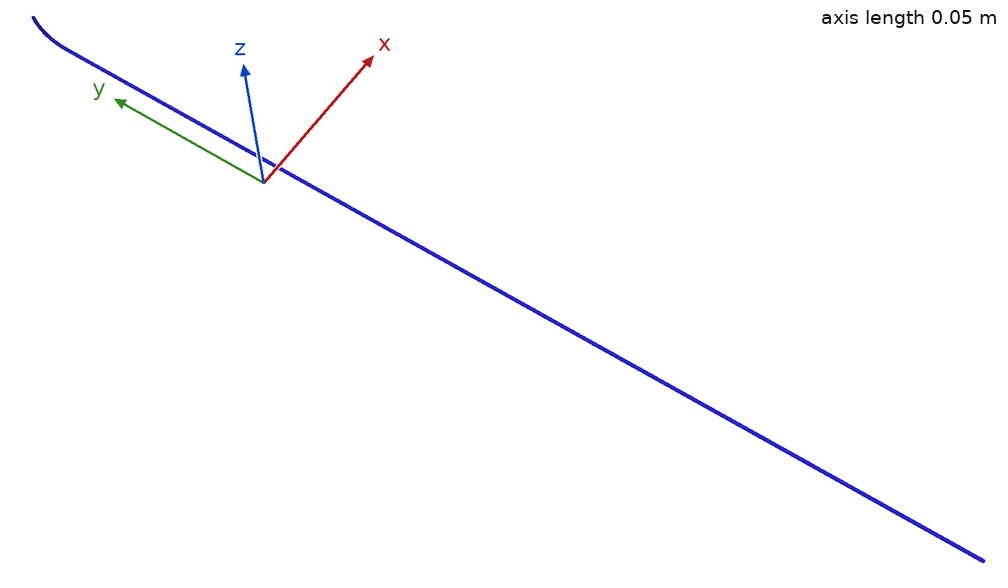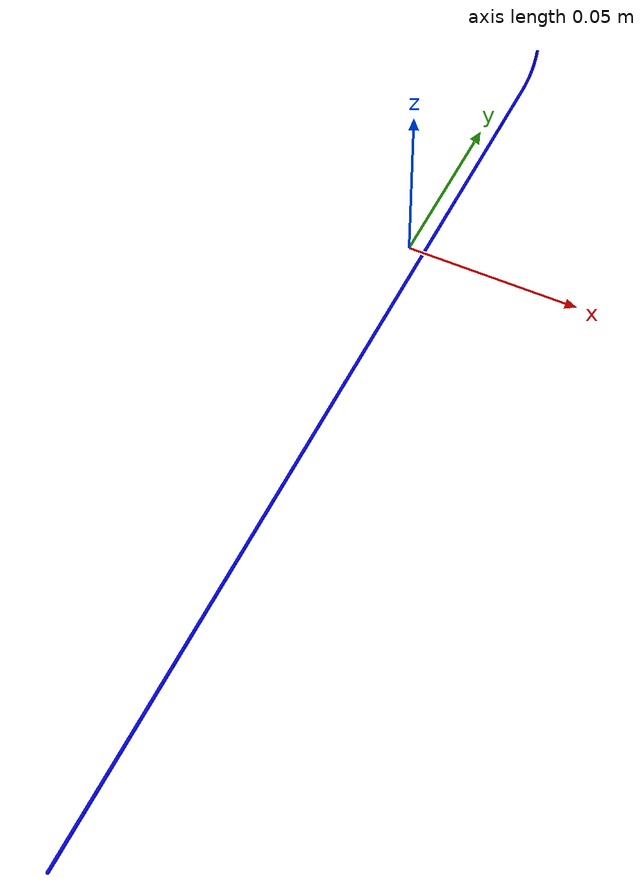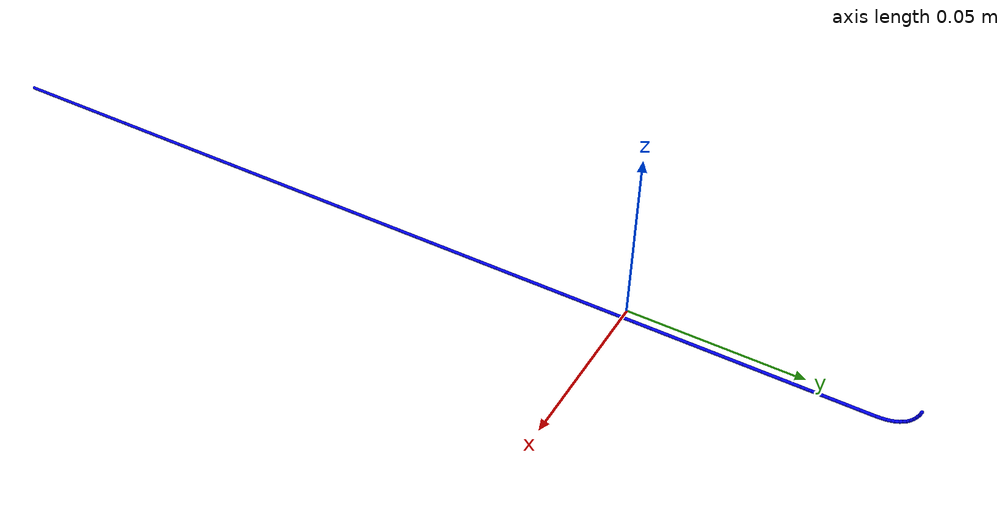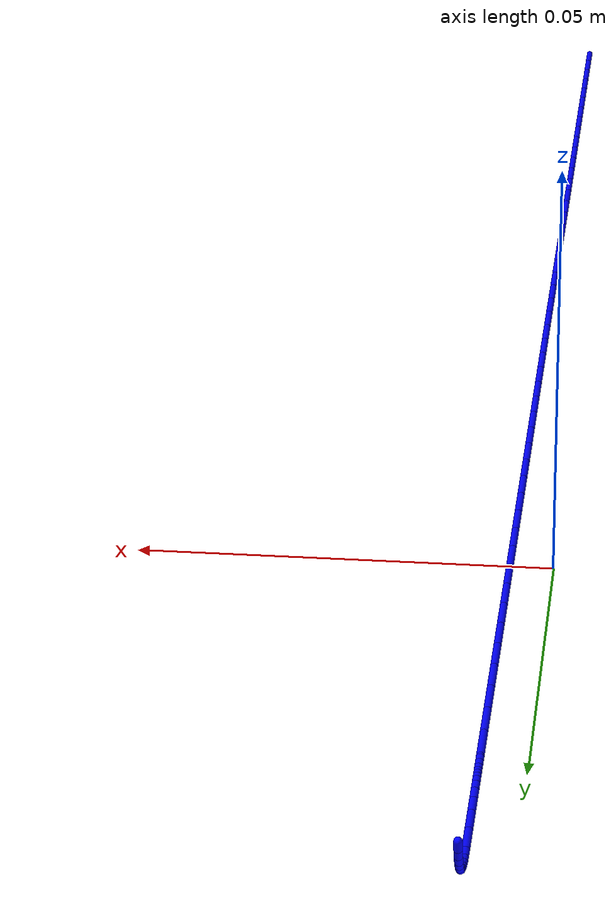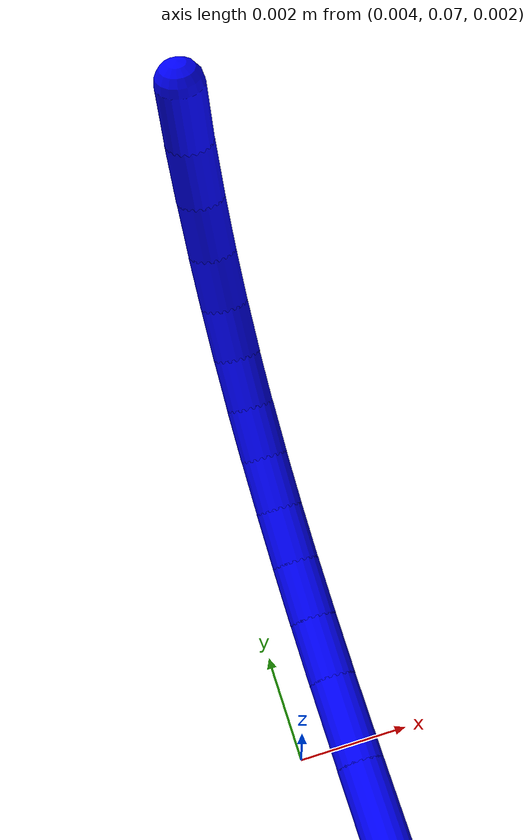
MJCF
<mujoco model="guidewire">
    <compiler angle="radian" />

    <default>
        <default class="guidewire_tip">
            <geom type="capsule" condim="3" margin="0.003" contype="1" conaffinity="2" />
            <default class="guidewire">
                <geom rgba="0 0 1 1" />
            </default>
            <default class="tip">
                <geom rgba="0 0 1 1" />
            </default>
        </default>
    </default>

    <extension>
        <plugin plugin="mujoco.elasticity.cable">
            <instance name="compositeguidewire">
                <config key="bend" value="2e8" />
                <config key="vmax" value="0.05" />
            </instance>
            <instance name="compositetip">
                <config key="bend" value="5e6" />
                <config key="vmax" value="0.05" />
            </instance>
        </plugin>
    </extension>

  <extension>
    <plugin plugin="mujoco.pid">
      <instance name="slider-pid">
        <config key="kp" value="0.05"></config>
        <config key="slewmax" value="4"></config>
      </instance>
      <instance name="rotator-pid">
        <config key="kp" value="0.1"></config>
        <config key="kd" value="0.01"></config>
        <config key="imax" value="0.0 1"></config>
        <config key="slewmax" value="4"></config>
      </instance>
    </plugin>
  </extension>

    <actuator>
        <plugin name="slider" ctrllimited="true" actdim="1" ctrlrange="0 0.20" instance="slider-pid" joint="slider" forcerange="-0.01 0.01" />
        <plugin name="rotator" ctrllimited="true" actdim="1" ctrlrange="-200 200" instance="rotator-pid" joint="rotator" forcerange="-1 1" />
    </actuator>

    <custom>
        <text name="composite_guidewire" data="rope_guidewire" />
        <text name="composite_tip" data="rope_tip" />
    </custom>

    <worldbody>
        <frame>
            <body name="guidewire" childclass="guidewire" pos="0.005 -0.2 0.002"
                quat="0.707107 0 0 0.707107">
                <joint name="slider" pos="0 0 0" axis="1 0 0" type="slide" limited="true"
                    range="-0.2 0.2" damping="1" />
                <joint name="rotator" pos="0 0 0" axis="1 0 0" damping="1" />
                <site name="test" pos="0 0.25 0" group="3" />
                <body name="guidewireB_first">
                    <geom name="guidewireG0" size="0.000445 0.00255102" pos="0.00255102 0 0"
                        quat="0.707107 0 -0.707107 0" />
                    <site name="guidewireS_first" pos="0 0 0" group="3" />
                    <plugin instance="compositeguidewire" />
                    <body name="guidewireB_1" pos="0.00510204 0 0">
                        <joint name="guidewireJ_1" pos="0 0 0" type="ball" group="3"
                            actuatorfrclimited="false" damping="0.015" />
                        <geom name="guidewireG1" size="0.000445 0.00255102" pos="0.00255102 0 0"
                            quat="0.707107 0 -0.707107 0" />
                        <plugin instance="compositeguidewire" />
                        <body name="guidewireB_2" pos="0.00510204 0 0">
                            <joint name="guidewireJ_2" pos="0 0 0" type="ball" group="3"
                                actuatorfrclimited="false" damping="0.015" />
                            <geom name="guidewireG2" size="0.000445 0.00255102" pos="0.00255102 0 0"
                                quat="0.707107 0 -0.707107 0" />
                            <plugin instance="compositeguidewire" />
                            <body name="guidewireB_3" pos="0.00510204 0 0">
                                <joint name="guidewireJ_3" pos="0 0 0" type="ball" group="3"
                                    actuatorfrclimited="false" damping="0.015" />
                                <geom name="guidewireG3" size="0.000445 0.00255102"
                                    pos="0.00255102 0 0" quat="0.707107 0 -0.707107 0" />
                                <plugin instance="compositeguidewire" />
                                <body name="guidewireB_4" pos="0.00510204 0 0">
                                    <joint name="guidewireJ_4" pos="0 0 0" type="ball" group="3"
                                        actuatorfrclimited="false" damping="0.015" />
                                    <geom name="guidewireG4" size="0.000445 0.00255102"
                                        pos="0.00255102 0 0" quat="0.707107 0 -0.707107 0" />
                                    <plugin instance="compositeguidewire" />
                                    <body name="guidewireB_5" pos="0.00510204 0 0">
                                        <joint name="guidewireJ_5" pos="0 0 0" type="ball" group="3"
                                            actuatorfrclimited="false" damping="0.015" />
                                        <geom name="guidewireG5" size="0.000445 0.00255102"
                                            pos="0.00255102 0 0" quat="0.707107 0 -0.707107 0" />
                                        <plugin instance="compositeguidewire" />
                                        <body name="guidewireB_6" pos="0.00510204 0 0">
                                            <joint name="guidewireJ_6" pos="0 0 0" type="ball"
                                                group="3" actuatorfrclimited="false" damping="0.015" />
                                            <geom name="guidewireG6" size="0.000445 0.00255102"
                                                pos="0.00255102 0 0" quat="0.707107 0 -0.707107 0" />
                                            <plugin instance="compositeguidewire" />
                                            <body name="guidewireB_7" pos="0.00510204 0 0">
                                                <joint name="guidewireJ_7" pos="0 0 0" type="ball"
                                                    group="3" actuatorfrclimited="false"
                                                    damping="0.015" />
                                                <geom name="guidewireG7" size="0.000445 0.00255102"
                                                    pos="0.00255102 0 0"
                                                    quat="0.707107 0 -0.707107 0" />
                                                <plugin instance="compositeguidewire" />
                                                <body name="guidewireB_8" pos="0.00510204 0 0">
                                                    <joint name="guidewireJ_8" pos="0 0 0"
                                                        type="ball" group="3"
                                                        actuatorfrclimited="false" damping="0.015" />
                                                    <geom name="guidewireG8"
                                                        size="0.000445 0.00255102"
                                                        pos="0.00255102 0 0"
                                                        quat="0.707107 0 -0.707107 0" />
                                                    <plugin instance="compositeguidewire" />
                                                    <body name="guidewireB_9" pos="0.00510204 0 0">
                                                        <joint name="guidewireJ_9" pos="0 0 0"
                                                            type="ball" group="3"
                                                            actuatorfrclimited="false"
                                                            damping="0.015" />
                                                        <geom name="guidewireG9"
                                                            size="0.000445 0.00255102"
                                                            pos="0.00255102 0 0"
                                                            quat="0.707107 0 -0.707107 0" />
                                                        <plugin instance="compositeguidewire" />
                                                        <body name="guidewireB_10"
                                                            pos="0.00510204 0 0">
                                                            <joint name="guidewireJ_10" pos="0 0 0"
                                                                type="ball" group="3"
                                                                actuatorfrclimited="false"
                                                                damping="0.015" />
                                                            <geom name="guidewireG10"
                                                                size="0.000445 0.00255102"
                                                                pos="0.00255102 0 0"
                                                                quat="0.707107 0 -0.707107 0" />
                                                            <plugin instance="compositeguidewire" />
                                                            <body name="guidewireB_11"
                                                                pos="0.00510204 0 0">
                                                                <joint name="guidewireJ_11"
                                                                    pos="0 0 0" type="ball"
                                                                    group="3"
                                                                    actuatorfrclimited="false"
                                                                    damping="0.015" />
                                                                <geom name="guidewireG11"
                                                                    size="0.000445 0.00255102"
                                                                    pos="0.00255102 0 0"
                                                                    quat="0.707107 0 -0.707107 0" />
                                                                <plugin
                                                                    instance="compositeguidewire" />
                                                                <body name="guidewireB_12"
                                                                    pos="0.00510204 0 0">
                                                                    <joint name="guidewireJ_12"
                                                                        pos="0 0 0" type="ball"
                                                                        group="3"
                                                                        actuatorfrclimited="false"
                                                                        damping="0.015" />
                                                                    <geom name="guidewireG12"
                                                                        size="0.000445 0.00255102"
                                                                        pos="0.00255102 0 0"
                                                                        quat="0.707107 0 -0.707107 0" />
                                                                    <plugin
                                                                        instance="compositeguidewire" />
                                                                    <body name="guidewireB_13"
                                                                        pos="0.00510204 0 0">
                                                                        <joint name="guidewireJ_13"
                                                                            pos="0 0 0" type="ball"
                                                                            group="3"
                                                                            actuatorfrclimited="false"
                                                                            damping="0.015" />
                                                                        <geom name="guidewireG13"
                                                                            size="0.000445 0.00255102"
                                                                            pos="0.00255102 0 0"
                                                                            quat="0.707107 0 -0.707107 0" />
                                                                        <plugin
                                                                            instance="compositeguidewire" />
                                                                        <body name="guidewireB_14"
                                                                            pos="0.00510205 0 0">
                                                                            <joint
                                                                                name="guidewireJ_14"
                                                                                pos="0 0 0"
                                                                                type="ball"
                                                                                group="3"
                                                                                actuatorfrclimited="false"
                                                                                damping="0.015" />
                                                                            <geom
                                                                                name="guidewireG14"
                                                                                size="0.000445 0.00255102"
                                                                                pos="0.00255102 0 0"
                                                                                quat="0.707107 0 -0.707107 0" />
                                                                            <plugin
                                                                                instance="compositeguidewire" />
                                                                            <body
                                                                                name="guidewireB_15"
                                                                                pos="0.00510204 0 0">
                                                                                <joint
                                                                                    name="guidewireJ_15"
                                                                                    pos="0 0 0"
                                                                                    type="ball"
                                                                                    group="3"
                                                                                    actuatorfrclimited="false"
                                                                                    damping="0.015" />
                                                                                <geom
                                                                                    name="guidewireG15"
                                                                                    size="0.000445 0.00255102"
                                                                                    pos="0.00255102 0 0"
                                                                                    quat="0.707107 0 -0.707107 0" />
                                                                                <plugin
                                                                                    instance="compositeguidewire" />
                                                                                <body
                                                                                    name="guidewireB_16"
                                                                                    pos="0.00510204 0 0">
                                                                                    <joint
                                                                                        name="guidewireJ_16"
                                                                                        pos="0 0 0"
                                                                                        type="ball"
                                                                                        group="3"
                                                                                        actuatorfrclimited="false"
                                                                                        damping="0.015" />
                                                                                    <geom
                                                                                        name="guidewireG16"
                                                                                        size="0.000445 0.00255102"
                                                                                        pos="0.00255102 0 0"
                                                                                        quat="0.707107 0 -0.707107 0" />
                                                                                    <plugin
                                                                                        instance="compositeguidewire" />
                                                                                    <body
                                                                                        name="guidewireB_17"
                                                                                        pos="0.00510205 0 0">
                                                                                        <joint
                                                                                            name="guidewireJ_17"
                                                                                            pos="0 0 0"
                                                                                            type="ball"
                                                                                            group="3"
                                                                                            actuatorfrclimited="false"
                                                                                            damping="0.015" />
                                                                                        <geom
                                                                                            name="guidewireG17"
                                                                                            size="0.000445 0.00255102"
                                                                                            pos="0.00255102 0 0"
                                                                                            quat="0.707107 0 -0.707107 0" />
                                                                                        <plugin
                                                                                            instance="compositeguidewire" />
                                                                                        <body
                                                                                            name="guidewireB_18"
                                                                                            pos="0.00510204 0 0">
                                                                                            <joint
                                                                                                name="guidewireJ_18"
                                                                                                pos="0 0 0"
                                                                                                type="ball"
                                                                                                group="3"
                                                                                                actuatorfrclimited="false"
                                                                                                damping="0.015" />
                                                                                            <geom
                                                                                                name="guidewireG18"
                                                                                                size="0.000445 0.00255102"
                                                                                                pos="0.00255102 0 0"
                                                                                                quat="0.707107 0 -0.707107 0" />
                                                                                            <plugin
                                                                                                instance="compositeguidewire" />
                                                                                            <body
                                                                                                name="guidewireB_19"
                                                                                                pos="0.00510204 0 0">
                                                                                                <joint
                                                                                                    name="guidewireJ_19"
                                                                                                    pos="0 0 0"
                                                                                                    type="ball"
                                                                                                    group="3"
                                                                                                    actuatorfrclimited="false"
                                                                                                    damping="0.015" />
                                                                                                <geom
                                                                                                    name="guidewireG19"
                                                                                                    size="0.000445 0.00255102"
                                                                                                    pos="0.00255102 0 0"
                                                                                                    quat="0.707107 0 -0.707107 0" />
                                                                                                <plugin
                                                                                                    instance="compositeguidewire" />
                                                                                                <body
                                                                                                    name="guidewireB_20"
                                                                                                    pos="0.00510205 0 0">
                                                                                                    <joint
                                                                                                        name="guidewireJ_20"
                                                                                                        pos="0 0 0"
                                                                                                        type="ball"
                                                                                                        group="3"
                                                                                                        actuatorfrclimited="false"
                                                                                                        damping="0.015" />
                                                                                                    <geom
                                                                                                        name="guidewireG20"
                                                                                                        size="0.000445 0.00255102"
                                                                                                        pos="0.00255102 0 0"
                                                                                                        quat="0.707107 0 -0.707107 0" />
                                                                                                    <plugin
                                                                                                        instance="compositeguidewire" />
                                                                                                    <body
                                                                                                        name="guidewireB_21"
                                                                                                        pos="0.00510204 0 0">
                                                                                                        <joint
                                                                                                            name="guidewireJ_21"
                                                                                                            pos="0 0 0"
                                                                                                            type="ball"
                                                                                                            group="3"
                                                                                                            actuatorfrclimited="false"
                                                                                                            damping="0.015" />
                                                                                                        <geom
                                                                                                            name="guidewireG21"
                                                                                                            size="0.000445 0.00255102"
                                                                                                            pos="0.00255102 0 0"
                                                                                                            quat="0.707107 0 -0.707107 0" />
                                                                                                        <plugin
                                                                                                            instance="compositeguidewire" />
                                                                                                        <body
                                                                                                            name="guidewireB_22"
                                                                                                            pos="0.00510204 0 0">
                                                                                                            <joint
                                                                                                                name="guidewireJ_22"
                                                                                                                pos="0 0 0"
                                                                                                                type="ball"
                                                                                                                group="3"
                                                                                                                actuatorfrclimited="false"
                                                                                                                damping="0.015" />
                                                                                                            <geom
                                                                                                                name="guidewireG22"
                                                                                                                size="0.000445 0.00255102"
                                                                                                                pos="0.00255102 0 0"
                                                                                                                quat="0.707107 0 -0.707107 0" />
                                                                                                            <plugin
                                                                                                                instance="compositeguidewire" />
                                                                                                            <body
                                                                                                                name="guidewireB_23"
                                                                                                                pos="0.00510205 0 0">
                                                                                                                <joint
                                                                                                                    name="guidewireJ_23"
                                                                                                                    pos="0 0 0"
                                                                                                                    type="ball"
                                                                                                                    group="3"
                                                                                                                    actuatorfrclimited="false"
                                                                                                                    damping="0.015" />
                                                                                                                <geom
                                                                                                                    name="guidewireG23"
                                                                                                                    size="0.000445 0.00255102"
                                                                                                                    pos="0.00255102 0 0"
                                                                                                                    quat="0.707107 0 -0.707107 0" />
                                                                                                                <plugin
                                                                                                                    instance="compositeguidewire" />
                                                                                                                <body
                                                                                                                    name="guidewireB_24"
                                                                                                                    pos="0.00510204 0 0">
                                                                                                                    <joint
                                                                                                                        name="guidewireJ_24"
                                                                                                                        pos="0 0 0"
                                                                                                                        type="ball"
                                                                                                                        group="3"
                                                                                                                        actuatorfrclimited="false"
                                                                                                                        damping="0.015" />
                                                                                                                    <geom
                                                                                                                        name="guidewireG24"
                                                                                                                        size="0.000445 0.00255102"
                                                                                                                        pos="0.00255102 0 0"
                                                                                                                        quat="0.707107 0 -0.707107 0" />
                                                                                                                    <plugin
                                                                                                                        instance="compositeguidewire" />
                                                                                                                    <body
                                                                                                                        name="guidewireB_25"
                                                                                                                        pos="0.00510204 0 0">
                                                                                                                        <joint
                                                                                                                            name="guidewireJ_25"
                                                                                                                            pos="0 0 0"
                                                                                                                            type="ball"
                                                                                                                            group="3"
                                                                                                                            actuatorfrclimited="false"
                                                                                                                            damping="0.015" />
                                                                                                                        <geom
                                                                                                                            name="guidewireG25"
                                                                                                                            size="0.000445 0.00255102"
                                                                                                                            pos="0.00255102 0 0"
                                                                                                                            quat="0.707107 0 -0.707107 0" />
                                                                                                                        <plugin
                                                                                                                            instance="compositeguidewire" />
                                                                                                                        <body
                                                                                                                            name="guidewireB_26"
                                                                                                                            pos="0.00510204 0 0">
                                                                                                                            <joint
                                                                                                                                name="guidewireJ_26"
                                                                                                                                pos="0 0 0"
                                                                                                                                type="ball"
                                                                                                                                group="3"
                                                                                                                                actuatorfrclimited="false"
                                                                                                                                damping="0.015" />
                                                                                                                            <geom
                                                                                                                                name="guidewireG26"
                                                                                                                                size="0.000445 0.00255102"
                                                                                                                                pos="0.00255102 0 0"
                                                                                                                                quat="0.707107 0 -0.707107 0" />
                                                                                                                            <plugin
                                                                                                                                instance="compositeguidewire" />
                                                                                                                            <body
                                                                                                                                name="guidewireB_27"
                                                                                                                                pos="0.00510204 0 0">
                                                                                                                                <joint
                                                                                                                                    name="guidewireJ_27"
                                                                                                                                    pos="0 0 0"
                                                                                                                                    type="ball"
                                                                                                                                    group="3"
                                                                                                                                    actuatorfrclimited="false"
                                                                                                                                    damping="0.015" />
                                                                                                                                <geom
                                                                                                                                    name="guidewireG27"
                                                                                                                                    size="0.000445 0.00255103"
                                                                                                                                    pos="0.00255103 0 0"
                                                                                                                                    quat="0.707107 0 -0.707107 0" />
                                                                                                                                <plugin
                                                                                                                                    instance="compositeguidewire" />
                                                                                                                                <body
                                                                                                                                    name="guidewireB_28"
                                                                                                                                    pos="0.00510205 0 0">
                                                                                                                                    <joint
                                                                                                                                        name="guidewireJ_28"
                                                                                                                                        pos="0 0 0"
                                                                                                                                        type="ball"
                                                                                                                                        group="3"
                                                                                                                                        actuatorfrclimited="false"
                                                                                                                                        damping="0.015" />
                                                                                                                                    <geom
                                                                                                                                        name="guidewireG28"
                                                                                                                                        size="0.000445 0.00255102"
                                                                                                                                        pos="0.00255102 0 0"
                                                                                                                                        quat="0.707107 0 -0.707107 0" />
                                                                                                                                    <plugin
                                                                                                                                        instance="compositeguidewire" />
                                                                                                                                    <body
                                                                                                                                        name="guidewireB_29"
                                                                                                                                        pos="0.00510204 0 0">
                                                                                                                                        <joint
                                                                                                                                            name="guidewireJ_29"
                                                                                                                                            pos="0 0 0"
                                                                                                                                            type="ball"
                                                                                                                                            group="3"
                                                                                                                                            actuatorfrclimited="false"
                                                                                                                                            damping="0.015" />
                                                                                                                                        <geom
                                                                                                                                            name="guidewireG29"
                                                                                                                                            size="0.000445 0.00255102"
                                                                                                                                            pos="0.00255102 0 0"
                                                                                                                                            quat="0.707107 0 -0.707107 0" />
                                                                                                                                        <plugin
                                                                                                                                            instance="compositeguidewire" />
                                                                                                                                        <body
                                                                                                                                            name="guidewireB_30"
                                                                                                                                            pos="0.00510204 0 0">
                                                                                                                                            <joint
                                                                                                                                                name="guidewireJ_30"
                                                                                                                                                pos="0 0 0"
                                                                                                                                                type="ball"
                                                                                                                                                group="3"
                                                                                                                                                actuatorfrclimited="false"
                                                                                                                                                damping="0.015" />
                                                                                                                                            <geom
                                                                                                                                                name="guidewireG30"
                                                                                                                                                size="0.000445 0.00255102"
                                                                                                                                                pos="0.00255102 0 0"
                                                                                                                                                quat="0.707107 0 -0.707107 0" />
                                                                                                                                            <plugin
                                                                                                                                                instance="compositeguidewire" />
                                                                                                                                            <body
                                                                                                                                                name="guidewireB_31"
                                                                                                                                                pos="0.00510204 0 0">
                                                                                                                                                <joint
                                                                                                                                                    name="guidewireJ_31"
                                                                                                                                                    pos="0 0 0"
                                                                                                                                                    type="ball"
                                                                                                                                                    group="3"
                                                                                                                                                    actuatorfrclimited="false"
                                                                                                                                                    damping="0.015" />
                                                                                                                                                <geom
                                                                                                                                                    name="guidewireG31"
                                                                                                                                                    size="0.000445 0.00255102"
                                                                                                                                                    pos="0.00255102 0 0"
                                                                                                                                                    quat="0.707107 0 -0.707107 0" />
                                                                                                                                                <plugin
                                                                                                                                                    instance="compositeguidewire" />
                                                                                                                                                <body
                                                                                                                                                    name="guidewireB_32"
                                                                                                                                                    pos="0.00510204 0 0">
                                                                                                                                                    <joint
                                                                                                                                                        name="guidewireJ_32"
                                                                                                                                                        pos="0 0 0"
                                                                                                                                                        type="ball"
                                                                                                                                                        group="3"
                                                                                                                                                        actuatorfrclimited="false"
                                                                                                                                                        damping="0.015" />
                                                                                                                                                    <geom
                                                                                                                                                        name="guidewireG32"
                                                                                                                                                        size="0.000445 0.00255102"
                                                                                                                                                        pos="0.00255102 0 0"
                                                                                                                                                        quat="0.707107 0 -0.707107 0" />
                                                                                                                                                    <plugin
                                                                                                                                                        instance="compositeguidewire" />
                                                                                                                                                    <body
                                                                                                                                                        name="guidewireB_33"
                                                                                                                                                        pos="0.00510204 0 0">
                                                                                                                                                        <joint
                                                                                                                                                            name="guidewireJ_33"
                                                                                                                                                            pos="0 0 0"
                                                                                                                                                            type="ball"
                                                                                                                                                            group="3"
                                                                                                                                                            actuatorfrclimited="false"
                                                                                                                                                            damping="0.015" />
                                                                                                                                                        <geom
                                                                                                                                                            name="guidewireG33"
                                                                                                                                                            size="0.000445 0.00255103"
                                                                                                                                                            pos="0.00255103 0 0"
                                                                                                                                                            quat="0.707107 0 -0.707107 0" />
                                                                                                                                                        <plugin
                                                                                                                                                            instance="compositeguidewire" />
                                                                                                                                                        <body
                                                                                                                                                            name="guidewireB_34"
                                                                                                                                                            pos="0.00510205 0 0">
                                                                                                                                                            <joint
                                                                                                                                                                name="guidewireJ_34"
                                                                                                                                                                pos="0 0 0"
                                                                                                                                                                type="ball"
                                                                                                                                                                group="3"
                                                                                                                                                                actuatorfrclimited="false"
                                                                                                                                                                damping="0.015" />
                                                                                                                                                            <geom
                                                                                                                                                                name="guidewireG34"
                                                                                                                                                                size="0.000445 0.00255102"
                                                                                                                                                                pos="0.00255102 0 0"
                                                                                                                                                                quat="0.707107 0 -0.707107 0" />
                                                                                                                                                            <plugin
                                                                                                                                                                instance="compositeguidewire" />
                                                                                                                                                            <body
                                                                                                                                                                name="guidewireB_35"
                                                                                                                                                                pos="0.00510204 0 0">
                                                                                                                                                                <joint
                                                                                                                                                                    name="guidewireJ_35"
                                                                                                                                                                    pos="0 0 0"
                                                                                                                                                                    type="ball"
                                                                                                                                                                    group="3"
                                                                                                                                                                    actuatorfrclimited="false"
                                                                                                                                                                    damping="0.015" />
                                                                                                                                                                <geom
                                                                                                                                                                    name="guidewireG35"
                                                                                                                                                                    size="0.000445 0.00255102"
                                                                                                                                                                    pos="0.00255102 0 0"
                                                                                                                                                                    quat="0.707107 0 -0.707107 0" />
                                                                                                                                                                <plugin
                                                                                                                                                                    instance="compositeguidewire" />
                                                                                                                                                                <body
                                                                                                                                                                    name="guidewireB_36"
                                                                                                                                                                    pos="0.00510204 0 0">
                                                                                                                                                                    <joint
                                                                                                                                                                        name="guidewireJ_36"
                                                                                                                                                                        pos="0 0 0"
                                                                                                                                                                        type="ball"
                                                                                                                                                                        group="3"
                                                                                                                                                                        actuatorfrclimited="false"
                                                                                                                                                                        damping="0.015" />
                                                                                                                                                                    <geom
                                                                                                                                                                        name="guidewireG36"
                                                                                                                                                                        size="0.000445 0.00255102"
                                                                                                                                                                        pos="0.00255102 0 0"
                                                                                                                                                                        quat="0.707107 0 -0.707107 0" />
                                                                                                                                                                    <plugin
                                                                                                                                                                        instance="compositeguidewire" />
                                                                                                                                                                    <body
                                                                                                                                                                        name="guidewireB_37"
                                                                                                                                                                        pos="0.00510204 0 0">
                                                                                                                                                                        <joint
                                                                                                                                                                            name="guidewireJ_37"
                                                                                                                                                                            pos="0 0 0"
                                                                                                                                                                            type="ball"
                                                                                                                                                                            group="3"
                                                                                                                                                                            actuatorfrclimited="false"
                                                                                                                                                                            damping="0.015" />
                                                                                                                                                                        <geom
                                                                                                                                                                            name="guidewireG37"
                                                                                                                                                                            size="0.000445 0.00255102"
                                                                                                                                                                            pos="0.00255102 0 0"
                                                                                                                                                                            quat="0.707107 0 -0.707107 0" />
                                                                                                                                                                        <plugin
                                                                                                                                                                            instance="compositeguidewire" />
                                                                                                                                                                        <body
                                                                                                                                                                            name="guidewireB_38"
                                                                                                                                                                            pos="0.00510204 0 0">
                                                                                                                                                                            <joint
                                                                                                                                                                                name="guidewireJ_38"
                                                                                                                                                                                pos="0 0 0"
                                                                                                                                                                                type="ball"
                                                                                                                                                                                group="3"
                                                                                                                                                                                actuatorfrclimited="false"
                                                                                                                                                                                damping="0.015" />
                                                                                                                                                                            <geom
                                                                                                                                                                                name="guidewireG38"
                                                                                                                                                                                size="0.000445 0.00255102"
                                                                                                                                                                                pos="0.00255102 0 0"
                                                                                                                                                                                quat="0.707107 0 -0.707107 0" />
                                                                                                                                                                            <plugin
                                                                                                                                                                                instance="compositeguidewire" />
                                                                                                                                                                            <body
                                                                                                                                                                                name="guidewireB_39"
                                                                                                                                                                                pos="0.00510204 0 0">
                                                                                                                                                                                <joint
                                                                                                                                                                                    name="guidewireJ_39"
                                                                                                                                                                                    pos="0 0 0"
                                                                                                                                                                                    type="ball"
                                                                                                                                                                                    group="3"
                                                                                                                                                                                    actuatorfrclimited="false"
                                                                                                                                                                                    damping="0.015" />
                                                                                                                                                                                <geom
                                                                                                                                                                                    name="guidewireG39"
                                                                                                                                                                                    size="0.000445 0.00255103"
                                                                                                                                                                                    pos="0.00255103 0 0"
                                                                                                                                                                                    quat="0.707107 0 -0.707107 0" />
                                                                                                                                                                                <plugin
                                                                                                                                                                                    instance="compositeguidewire" />
                                                                                                                                                                                <body
                                                                                                                                                                                    name="guidewireB_40"
                                                                                                                                                                                    pos="0.00510205 0 0">
                                                                                                                                                                                    <joint
                                                                                                                                                                                        name="guidewireJ_40"
                                                                                                                                                                                        pos="0 0 0"
                                                                                                                                                                                        type="ball"
                                                                                                                                                                                        group="3"
                                                                                                                                                                                        actuatorfrclimited="false"
                                                                                                                                                                                        damping="0.015" />
                                                                                                                                                                                    <geom
                                                                                                                                                                                        name="guidewireG40"
                                                                                                                                                                                        size="0.000445 0.00255102"
                                                                                                                                                                                        pos="0.00255102 0 0"
                                                                                                                                                                                        quat="0.707107 0 -0.707107 0" />
                                                                                                                                                                                    <plugin
                                                                                                                                                                                        instance="compositeguidewire" />
                                                                                                                                                                                    <body
                                                                                                                                                                                        name="guidewireB_41"
                                                                                                                                                                                        pos="0.00510204 0 0">
                                                                                                                                                                                        <joint
                                                                                                                                                                                            name="guidewireJ_41"
                                                                                                                                                                                            pos="0 0 0"
                                                                                                                                                                                            type="ball"
                                                                                                                                                                                            group="3"
                                                                                                                                                                                            actuatorfrclimited="false"
                                                                                                                                                                                            damping="0.015" />
                                                                                                                                                                                        <geom
                                                                                                                                                                                            name="guidewireG41"
                                                                                                                                                                                            size="0.000445 0.00255102"
                                                                                                                                                                                            pos="0.00255102 0 0"
                                                                                                                                                                                            quat="0.707107 0 -0.707107 0" />
                                                                                                                                                                                        <plugin
                                                                                                                                                                                            instance="compositeguidewire" />
                                                                                                                                                                                        <body
                                                                                                                                                                                            name="guidewireB_42"
                                                                                                                                                                                            pos="0.00510204 0 0">
                                                                                                                                                                                            <joint
                                                                                                                                                                                                name="guidewireJ_42"
                                                                                                                                                                                                pos="0 0 0"
                                                                                                                                                                                                type="ball"
                                                                                                                                                                                                group="3"
                                                                                                                                                                                                actuatorfrclimited="false"
                                                                                                                                                                                                damping="0.015" />
                                                                                                                                                                                            <geom
                                                                                                                                                                                                name="guidewireG42"
                                                                                                                                                                                                size="0.000445 0.00255102"
                                                                                                                                                                                                pos="0.00255102 0 0"
                                                                                                                                                                                                quat="0.707107 0 -0.707107 0" />
                                                                                                                                                                                            <plugin
                                                                                                                                                                                                instance="compositeguidewire" />
                                                                                                                                                                                            <body
                                                                                                                                                                                                name="guidewireB_43"
                                                                                                                                                                                                pos="0.00510204 0 0">
                                                                                                                                                                                                <joint
                                                                                                                                                                                                    name="guidewireJ_43"
                                                                                                                                                                                                    pos="0 0 0"
                                                                                                                                                                                                    type="ball"
                                                                                                                                                                                                    group="3"
                                                                                                                                                                                                    actuatorfrclimited="false"
                                                                                                                                                                                                    damping="0.015" />
                                                                                                                                                                                                <geom
                                                                                                                                                                                                    name="guidewireG43"
                                                                                                                                                                                                    size="0.000445 0.00255102"
                                                                                                                                                                                                    pos="0.00255102 0 0"
                                                                                                                                                                                                    quat="0.707107 0 -0.707107 0" />
                                                                                                                                                                                                <plugin
                                                                                                                                                                                                    instance="compositeguidewire" />
                                                                                                                                                                                                <body
                                                                                                                                                                                                    name="guidewireB_44"
                                                                                                                                                                                                    pos="0.00510204 0 0">
                                                                                                                                                                                                    <joint
                                                                                                                                                                                                        name="guidewireJ_44"
                                                                                                                                                                                                        pos="0 0 0"
                                                                                                                                                                                                        type="ball"
                                                                                                                                                                                                        group="3"
                                                                                                                                                                                                        actuatorfrclimited="false"
                                                                                                                                                                                                        damping="0.015" />
                                                                                                                                                                                                    <geom
                                                                                                                                                                                                        name="guidewireG44"
                                                                                                                                                                                                        size="0.000445 0.00255102"
                                                                                                                                                                                                        pos="0.00255102 0 0"
                                                                                                                                                                                                        quat="0.707107 0 -0.707107 0" />
                                                                                                                                                                                                    <plugin
                                                                                                                                                                                                        instance="compositeguidewire" />
                                                                                                                                                                                                    <body
                                                                                                                                                                                                        name="guidewireB_45"
                                                                                                                                                                                                        pos="0.00510204 0 0">
                                                                                                                                                                                                        <joint
                                                                                                                                                                                                            name="guidewireJ_45"
                                                                                                                                                                                                            pos="0 0 0"
                                                                                                                                                                                                            type="ball"
                                                                                                                                                                                                            group="3"
                                                                                                                                                                                                            actuatorfrclimited="false"
                                                                                                                                                                                                            damping="0.015" />
                                                                                                                                                                                                        <geom
                                                                                                                                                                                                            name="guidewireG45"
                                                                                                                                                                                                            size="0.000445 0.00255103"
                                                                                                                                                                                                            pos="0.00255103 0 0"
                                                                                                                                                                                                            quat="0.707107 0 -0.707107 0" />
                                                                                                                                                                                                        <plugin
                                                                                                                                                                                                            instance="compositeguidewire" />
                                                                                                                                                                                                        <body
                                                                                                                                                                                                            name="guidewireB_46"
                                                                                                                                                                                                            pos="0.00510205 0 0">
                                                                                                                                                                                                            <joint
                                                                                                                                                                                                                name="guidewireJ_46"
                                                                                                                                                                                                                pos="0 0 0"
                                                                                                                                                                                                                type="ball"
                                                                                                                                                                                                                group="3"
                                                                                                                                                                                                                actuatorfrclimited="false"
                                                                                                                                                                                                                damping="0.015" />
                                                                                                                                                                                                            <geom
                                                                                                                                                                                                                name="guidewireG46"
                                                                                                                                                                                                                size="0.000445 0.00255102"
                                                                                                                                                                                                                pos="0.00255102 0 0"
                                                                                                                                                                                                                quat="0.707107 0 -0.707107 0" />
                                                                                                                                                                                                            <plugin
                                                                                                                                                                                                                instance="compositeguidewire" />
                                                                                                                                                                                                            <body
                                                                                                                                                                                                                name="guidewireB_47"
                                                                                                                                                                                                                pos="0.00510204 0 0">
                                                                                                                                                                                                                <joint
                                                                                                                                                                                                                    name="guidewireJ_47"
                                                                                                                                                                                                                    pos="0 0 0"
                                                                                                                                                                                                                    type="ball"
                                                                                                                                                                                                                    group="3"
                                                                                                                                                                                                                    actuatorfrclimited="false"
                                                                                                                                                                                                                    damping="0.015" />
                                                                                                                                                                                                                <geom
                                                                                                                                                                                                                    name="guidewireG47"
                                                                                                                                                                                                                    size="0.000445 0.00255102"
                                                                                                                                                                                                                    pos="0.00255102 0 0"
                                                                                                                                                                                                                    quat="0.707107 0 -0.707107 0" />
                                                                                                                                                                                                                <plugin
                                                                                                                                                                                                                    instance="compositeguidewire" />
                                                                                                                                                                                                                <body
                                                                                                                                                                                                                    name="guidewireB_last"
                                                                                                                                                                                                                    pos="0.00510204 0 0">
                                                                                                                                                                                                                    <joint
                                                                                                                                                                                                                        name="guidewireJ_last"
                                                                                                                                                                                                                        pos="0 0 0"
                                                                                                                                                                                                                        type="ball"
                                                                                                                                                                                                                        group="3"
                                                                                                                                                                                                                        actuatorfrclimited="false"
                                                                                                                                                                                                                        damping="0.015" />
                                                                                                                                                                                                                    <geom
                                                                                                                                                                                                                        name="guidewireG48"
                                                                                                                                                                                                                        size="0.000445 0.00255102"
                                                                                                                                                                                                                        pos="0.00255102 0 0"
                                                                                                                                                                                                                        quat="0.707107 0 -0.707107 0" />
                                                                                                                                                                                                                    <site
                                                                                                                                                                                                                        name="guidewireS_last"
                                                                                                                                                                                                                        pos="0.00510204 0 0"
                                                                                                                                                                                                                        group="3" />
                                                                                                                                                                                                                    <plugin
                                                                                                                                                                                                                        instance="compositeguidewire" />
                                                                                                                                                                                                                    <body
                                                                                                                                                                                                                        name="tipB_first"
                                                                                                                                                                                                                        childclass="tip"
                                                                                                                                                                                                                        pos="0.00510204 0 0">
                                                                                                                                                                                                                        <joint
                                                                                                                                                                                                                            name="tipJ_first"
                                                                                                                                                                                                                            pos="0 0 0"
                                                                                                                                                                                                                            type="ball"
                                                                                                                                                                                                                            group="3"
                                                                                                                                                                                                                            actuatorfrclimited="false"
                                                                                                                                                                                                                            damping="0.015" />
                                                                                                                                                                                                                        <geom
                                                                                                                                                                                                                            name="tipG0"
                                                                                                                                                                                                                            size="0.000445 0.0001765"
                                                                                                                                                                                                                            pos="0.0001765 0 0"
                                                                                                                                                                                                                            quat="0.707107 0 -0.707107 0" />
                                                                                                                                                                                                                        <site
                                                                                                                                                                                                                            name="tipS_first"
                                                                                                                                                                                                                            pos="0 0 0"
                                                                                                                                                                                                                            group="3" />
                                                                                                                                                                                                                        <plugin
                                                                                                                                                                                                                            instance="compositetip" />
                                                                                                                                                                                                                        <body
                                                                                                                                                                                                                            name="tipB_1"
                                                                                                                                                                                                                            pos="0.000353 0 0">
                                                                                                                                                                                                                            <joint
                                                                                                                                                                                                                                name="tipJ_1"
                                                                                                                                                                                                                                pos="0 0 0"
                                                                                                                                                                                                                                type="ball"
                                                                                                                                                                                                                                group="3"
                                                                                                                                                                                                                                actuatorfrclimited="false"
                                                                                                                                                                                                                                damping="0.015" />
                                                                                                                                                                                                                            <geom
                                                                                                                                                                                                                                name="tipG1"
                                                                                                                                                                                                                                size="0.000445 0.0005035"
                                                                                                                                                                                                                                pos="0.0005035 0 0"
                                                                                                                                                                                                                                quat="0.707107 0 -0.707107 0" />
                                                                                                                                                                                                                            <plugin
                                                                                                                                                                                                                                instance="compositetip" />
                                                                                                                                                                                                                            <body
                                                                                                                                                                                                                                name="tipB_2"
                                                                                                                                                                                                                                pos="0.001007 0 0">
                                                                                                                                                                                                                                <joint
                                                                                                                                                                                                                                    name="tipJ_2"
                                                                                                                                                                                                                                    pos="0 0 0"
                                                                                                                                                                                                                                    type="ball"
                                                                                                                                                                                                                                    group="3"
                                                                                                                                                                                                                                    actuatorfrclimited="false"
                                                                                                                                                                                                                                    damping="0.015" />
                                                                                                                                                                                                                                <geom
                                                                                                                                                                                                                                    name="tipG2"
                                                                                                                                                                                                                                    size="0.000445 0.000506"
                                                                                                                                                                                                                                    pos="0.000506 0 0"
                                                                                                                                                                                                                                    quat="0.707107 0 -0.707107 0" />
                                                                                                                                                                                                                                <plugin
                                                                                                                                                                                                                                    instance="compositetip" />
                                                                                                                                                                                                                                <body
                                                                                                                                                                                                                                    name="tipB_3"
                                                                                                                                                                                                                                    pos="0.001012 0 0">
                                                                                                                                                                                                                                    <joint
                                                                                                                                                                                                                                        name="tipJ_3"
                                                                                                                                                                                                                                        pos="0 0 0"
                                                                                                                                                                                                                                        type="ball"
                                                                                                                                                                                                                                        group="3"
                                                                                                                                                                                                                                        actuatorfrclimited="false"
                                                                                                                                                                                                                                        damping="0.015" />
                                                                                                                                                                                                                                    <geom
                                                                                                                                                                                                                                        name="tipG3"
                                                                                                                                                                                                                                        size="0.000445 0.000368"
                                                                                                                                                                                                                                        pos="0.000368 0 0"
                                                                                                                                                                                                                                        quat="0.707107 0 -0.707107 0" />
                                                                                                                                                                                                                                    <plugin
                                                                                                                                                                                                                                        instance="compositetip" />
                                                                                                                                                                                                                                    <body
                                                                                                                                                                                                                                        name="tipB_4"
                                                                                                                                                                                                                                        pos="0.000736 0 0">
                                                                                                                                                                                                                                        <joint
                                                                                                                                                                                                                                            name="tipJ_4"
                                                                                                                                                                                                                                            pos="0 0 0"
                                                                                                                                                                                                                                            type="ball"
                                                                                                                                                                                                                                            group="3"
                                                                                                                                                                                                                                            actuatorfrclimited="false"
                                                                                                                                                                                                                                            damping="0.015" />
                                                                                                                                                                                                                                        <geom
                                                                                                                                                                                                                                            name="tipG4"
                                                                                                                                                                                                                                            size="0.000445 0.000298"
                                                                                                                                                                                                                                            pos="0.000298 0 0"
                                                                                                                                                                                                                                            quat="0.707107 0 -0.707107 0" />
                                                                                                                                                                                                                                        <plugin
                                                                                                                                                                                                                                            instance="compositetip" />
                                                                                                                                                                                                                                        <body
                                                                                                                                                                                                                                            name="tipB_5"
                                                                                                                                                                                                                                            pos="0.000596 0 0">
                                                                                                                                                                                                                                            <joint
                                                                                                                                                                                                                                                name="tipJ_5"
                                                                                                                                                                                                                                                pos="0 0 0"
                                                                                                                                                                                                                                                type="ball"
                                                                                                                                                                                                                                                group="3"
                                                                                                                                                                                                                                                actuatorfrclimited="false"
                                                                                                                                                                                                                                                damping="0.015" />
                                                                                                                                                                                                                                            <geom
                                                                                                                                                                                                                                                name="tipG5"
                                                                                                                                                                                                                                                size="0.000445 0.000298"
                                                                                                                                                                                                                                                pos="0.000298 0 0"
                                                                                                                                                                                                                                                quat="0.707107 0 -0.707107 0" />
                                                                                                                                                                                                                                            <plugin
                                                                                                                                                                                                                                                instance="compositetip" />
                                                                                                                                                                                                                                            <body
                                                                                                                                                                                                                                                name="tipB_6"
                                                                                                                                                                                                                                                pos="0.000596 0 0">
                                                                                                                                                                                                                                                <joint
                                                                                                                                                                                                                                                    name="tipJ_6"
                                                                                                                                                                                                                                                    pos="0 0 0"
                                                                                                                                                                                                                                                    type="ball"
                                                                                                                                                                                                                                                    group="3"
                                                                                                                                                                                                                                                    actuatorfrclimited="false"
                                                                                                                                                                                                                                                    damping="0.015" />
                                                                                                                                                                                                                                                <geom
                                                                                                                                                                                                                                                    name="tipG6"
                                                                                                                                                                                                                                                    size="0.000445 0.0003675"
                                                                                                                                                                                                                                                    pos="0.0003675 0 0"
                                                                                                                                                                                                                                                    quat="0.707107 0 -0.707107 0" />
                                                                                                                                                                                                                                                <plugin
                                                                                                                                                                                                                                                    instance="compositetip" />
                                                                                                                                                                                                                                                <body
                                                                                                                                                                                                                                                    name="tipB_7"
                                                                                                                                                                                                                                                    pos="0.000735 0 0">
                                                                                                                                                                                                                                                    <joint
                                                                                                                                                                                                                                                        name="tipJ_7"
                                                                                                                                                                                                                                                        pos="0 0 0"
                                                                                                                                                                                                                                                        type="ball"
                                                                                                                                                                                                                                                        group="3"
                                                                                                                                                                                                                                                        actuatorfrclimited="false"
                                                                                                                                                                                                                                                        damping="0.015" />
                                                                                                                                                                                                                                                    <geom
                                                                                                                                                                                                                                                        name="tipG7"
                                                                                                                                                                                                                                                        size="0.000445 0.000506"
                                                                                                                                                                                                                                                        pos="0.000506 0 0"
                                                                                                                                                                                                                                                        quat="0.707107 0 -0.707107 0" />
                                                                                                                                                                                                                                                    <plugin
                                                                                                                                                                                                                                                        instance="compositetip" />
                                                                                                                                                                                                                                                    <body
                                                                                                                                                                                                                                                        name="tipB_8"
                                                                                                                                                                                                                                                        pos="0.001012 0 0">
                                                                                                                                                                                                                                                        <joint
                                                                                                                                                                                                                                                            name="tipJ_8"
                                                                                                                                                                                                                                                            pos="0 0 0"
                                                                                                                                                                                                                                                            type="ball"
                                                                                                                                                                                                                                                            group="3"
                                                                                                                                                                                                                                                            actuatorfrclimited="false"
                                                                                                                                                                                                                                                            damping="0.015" />
                                                                                                                                                                                                                                                        <geom
                                                                                                                                                                                                                                                            name="tipG8"
                                                                                                                                                                                                                                                            size="0.000445 0.000715"
                                                                                                                                                                                                                                                            pos="0.000715 0 0"
                                                                                                                                                                                                                                                            quat="0.707107 0 -0.707107 0" />
                                                                                                                                                                                                                                                        <plugin
                                                                                                                                                                                                                                                            instance="compositetip" />
                                                                                                                                                                                                                                                        <body
                                                                                                                                                                                                                                                            name="tipB_9"
                                                                                                                                                                                                                                                            pos="0.00143 0 0">
                                                                                                                                                                                                                                                            <joint
                                                                                                                                                                                                                                                                name="tipJ_9"
                                                                                                                                                                                                                                                                pos="0 0 0"
                                                                                                                                                                                                                                                                type="ball"
                                                                                                                                                                                                                                                                group="3"
                                                                                                                                                                                                                                                                actuatorfrclimited="false"
                                                                                                                                                                                                                                                                damping="0.015" />
                                                                                                                                                                                                                                                            <geom
                                                                                                                                                                                                                                                                name="tipG9"
                                                                                                                                                                                                                                                                size="0.000445 0.0009925"
                                                                                                                                                                                                                                                                pos="0.0009925 0 0"
                                                                                                                                                                                                                                                                quat="0.707107 0 -0.707107 0" />
                                                                                                                                                                                                                                                            <plugin
                                                                                                                                                                                                                                                                instance="compositetip" />
                                                                                                                                                                                                                                                            <body
                                                                                                                                                                                                                                                                name="tipB_10"
                                                                                                                                                                                                                                                                pos="0.001985 0 0">
                                                                                                                                                                                                                                                                <joint
                                                                                                                                                                                                                                                                    name="tipJ_10"
                                                                                                                                                                                                                                                                    pos="0 0 0"
                                                                                                                                                                                                                                                                    type="ball"
                                                                                                                                                                                                                                                                    group="3"
                                                                                                                                                                                                                                                                    actuatorfrclimited="false"
                                                                                                                                                                                                                                                                    damping="0.015" />
                                                                                                                                                                                                                                                                <geom
                                                                                                                                                                                                                                                                    name="tipG10"
                                                                                                                                                                                                                                                                    size="0.000445 0.0013395"
                                                                                                                                                                                                                                                                    pos="0.0013395 0 0"
                                                                                                                                                                                                                                                                    quat="0.707107 0 -0.707107 0" />
                                                                                                                                                                                                                                                                <plugin
                                                                                                                                                                                                                                                                    instance="compositetip" />
                                                                                                                                                                                                                                                                <body
                                                                                                                                                                                                                                                                    name="tipB_11"
                                                                                                                                                                                                                                                                    pos="0.002679 0 0">
                                                                                                                                                                                                                                                                    <joint
                                                                                                                                                                                                                                                                        name="tipJ_11"
                                                                                                                                                                                                                                                                        pos="0 0 0"
                                                                                                                                                                                                                                                                        type="ball"
                                                                                                                                                                                                                                                                        group="3"
                                                                                                                                                                                                                                                                        actuatorfrclimited="false"
                                                                                                                                                                                                                                                                        damping="0.015" />
                                                                                                                                                                                                                                                                    <geom
                                                                                                                                                                                                                                                                        name="tipG11"
                                                                                                                                                                                                                                                                        size="0.000445 0.0017565"
                                                                                                                                                                                                                                                                        pos="0.0017565 0 0"
                                                                                                                                                                                                                                                                        quat="0.707107 0 -0.707107 0" />
                                                                                                                                                                                                                                                                    <plugin
                                                                                                                                                                                                                                                                        instance="compositetip" />
                                                                                                                                                                                                                                                                    <body
                                                                                                                                                                                                                                                                        name="tipB_12"
                                                                                                                                                                                                                                                                        pos="0.003513 0 0">
                                                                                                                                                                                                                                                                        <joint
                                                                                                                                                                                                                                                                            name="tipJ_12"
                                                                                                                                                                                                                                                                            pos="0 0 0"
                                                                                                                                                                                                                                                                            type="ball"
                                                                                                                                                                                                                                                                            group="3"
                                                                                                                                                                                                                                                                            actuatorfrclimited="false"
                                                                                                                                                                                                                                                                            damping="0.015" />
                                                                                                                                                                                                                                                                        <geom
                                                                                                                                                                                                                                                                            name="tipG12"
                                                                                                                                                                                                                                                                            size="0.000445 0.001971"
                                                                                                                                                                                                                                                                            pos="0.001971 0 0"
                                                                                                                                                                                                                                                                            quat="0.707107 0 -0.707107 0" />
                                                                                                                                                                                                                                                                        <plugin
                                                                                                                                                                                                                                                                            instance="compositetip" />
                                                                                                                                                                                                                                                                        <body
                                                                                                                                                                                                                                                                            name="tipB_13"
                                                                                                                                                                                                                                                                            pos="0.003942 0 0"
                                                                                                                                                                                                                                                                            quat="0.999385 0.0247856 -0.0247856 0.000614706">
                                                                                                                                                                                                                                                                            <joint
                                                                                                                                                                                                                                                                                name="tipJ_13"
                                                                                                                                                                                                                                                                                pos="0 0 0"
                                                                                                                                                                                                                                                                                type="ball"
                                                                                                                                                                                                                                                                                group="3"
                                                                                                                                                                                                                                                                                actuatorfrclimited="false"
                                                                                                                                                                                                                                                                                damping="0.015" />
                                                                                                                                                                                                                                                                            <geom
                                                                                                                                                                                                                                                                                name="tipG13"
                                                                                                                                                                                                                                                                                size="0.000445 0.000817005"
                                                                                                                                                                                                                                                                                pos="0.000817005 0 0"
                                                                                                                                                                                                                                                                                quat="0.707107 0 -0.707107 0" />
                                                                                                                                                                                                                                                                            <plugin
                                                                                                                                                                                                                                                                                instance="compositetip" />
                                                                                                                                                                                                                                                                            <body
                                                                                                                                                                                                                                                                                name="tipB_14"
                                                                                                                                                                                                                                                                                pos="0.00163401 0 0"
                                                                                                                                                                                                                                                                                quat="0.99831 0.0410694 -0.0409352 0.00372334">
                                                                                                                                                                                                                                                                                <joint
                                                                                                                                                                                                                                                                                    name="tipJ_14"
                                                                                                                                                                                                                                                                                    pos="0 0 0"
                                                                                                                                                                                                                                                                                    type="ball"
                                                                                                                                                                                                                                                                                    group="3"
                                                                                                                                                                                                                                                                                    actuatorfrclimited="false"
                                                                                                                                                                                                                                                                                    damping="0.015" />
                                                                                                                                                                                                                                                                                <geom
                                                                                                                                                                                                                                                                                    name="tipG14"
                                                                                                                                                                                                                                                                                    size="0.000445 0.000589615"
                                                                                                                                                                                                                                                                                    pos="0.000589615 0 0"
                                                                                                                                                                                                                                                                                    quat="0.707107 0 -0.707107 0" />
                                                                                                                                                                                                                                                                                <plugin
                                                                                                                                                                                                                                                                                    instance="compositetip" />
                                                                                                                                                                                                                                                                                <body
                                                                                                                                                                                                                                                                                    name="tipB_15"
                                                                                                                                                                                                                                                                                    pos="0.00117923 0 0"
                                                                                                                                                                                                                                                                                    quat="0.998447 0.0393768 -0.0388311 0.00671523">
                                                                                                                                                                                                                                                                                    <joint
                                                                                                                                                                                                                                                                                        name="tipJ_15"
                                                                                                                                                                                                                                                                                        pos="0 0 0"
                                                                                                                                                                                                                                                                                        type="ball"
                                                                                                                                                                                                                                                                                        group="3"
                                                                                                                                                                                                                                                                                        actuatorfrclimited="false"
                                                                                                                                                                                                                                                                                        damping="0.015" />
                                                                                                                                                                                                                                                                                    <geom
                                                                                                                                                                                                                                                                                        name="tipG15"
                                                                                                                                                                                                                                                                                        size="0.000445 0.000561922"
                                                                                                                                                                                                                                                                                        pos="0.000561922 0 0"
                                                                                                                                                                                                                                                                                        quat="0.707107 0 -0.707107 0" />
                                                                                                                                                                                                                                                                                    <plugin
                                                                                                                                                                                                                                                                                        instance="compositetip" />
                                                                                                                                                                                                                                                                                    <body
                                                                                                                                                                                                                                                                                        name="tipB_16"
                                                                                                                                                                                                                                                                                        pos="0.00112384 0 0"
                                                                                                                                                                                                                                                                                        quat="0.997954 0.0451918 -0.0437648 0.011451">
                                                                                                                                                                                                                                                                                        <joint
                                                                                                                                                                                                                                                                                            name="tipJ_16"
                                                                                                                                                                                                                                                                                            pos="0 0 0"
                                                                                                                                                                                                                                                                                            type="ball"
                                                                                                                                                                                                                                                                                            group="3"
                                                                                                                                                                                                                                                                                            actuatorfrclimited="false"
                                                                                                                                                                                                                                                                                            damping="0.015" />
                                                                                                                                                                                                                                                                                        <geom
                                                                                                                                                                                                                                                                                            name="tipG16"
                                                                                                                                                                                                                                                                                            size="0.000445 0.000537701"
                                                                                                                                                                                                                                                                                            pos="0.000537701 0 0"
                                                                                                                                                                                                                                                                                            quat="0.707107 0 -0.707107 0" />
                                                                                                                                                                                                                                                                                        <plugin
                                                                                                                                                                                                                                                                                            instance="compositetip" />
                                                                                                                                                                                                                                                                                        <body
                                                                                                                                                                                                                                                                                            name="tipB_17"
                                                                                                                                                                                                                                                                                            pos="0.0010754 0 0"
                                                                                                                                                                                                                                                                                            quat="0.997306 0.0518331 -0.048701 0.0179481">
                                                                                                                                                                                                                                                                                            <joint
                                                                                                                                                                                                                                                                                                name="tipJ_17"
                                                                                                                                                                                                                                                                                                pos="0 0 0"
                                                                                                                                                                                                                                                                                                type="ball"
                                                                                                                                                                                                                                                                                                group="3"
                                                                                                                                                                                                                                                                                                actuatorfrclimited="false"
                                                                                                                                                                                                                                                                                                damping="0.015" />
                                                                                                                                                                                                                                                                                            <geom
                                                                                                                                                                                                                                                                                                name="tipG17"
                                                                                                                                                                                                                                                                                                size="0.000445 0.000518989"
                                                                                                                                                                                                                                                                                                pos="0.000518989 0 0"
                                                                                                                                                                                                                                                                                                quat="0.707107 0 -0.707107 0" />
                                                                                                                                                                                                                                                                                            <plugin
                                                                                                                                                                                                                                                                                                instance="compositetip" />
                                                                                                                                                                                                                                                                                            <body
                                                                                                                                                                                                                                                                                                name="tipB_18"
                                                                                                                                                                                                                                                                                                pos="0.00103798 0 0"
                                                                                                                                                                                                                                                                                                quat="0.996691 0.0574259 -0.0514761 0.0256688">
                                                                                                                                                                                                                                                                                                <joint
                                                                                                                                                                                                                                                                                                    name="tipJ_18"
                                                                                                                                                                                                                                                                                                    pos="0 0 0"
                                                                                                                                                                                                                                                                                                    type="ball"
                                                                                                                                                                                                                                                                                                    group="3"
                                                                                                                                                                                                                                                                                                    actuatorfrclimited="false"
                                                                                                                                                                                                                                                                                                    damping="0.015" />
                                                                                                                                                                                                                                                                                                <geom
                                                                                                                                                                                                                                                                                                    name="tipG18"
                                                                                                                                                                                                                                                                                                    size="0.000445 0.000507055"
                                                                                                                                                                                                                                                                                                    pos="0.000507055 0 0"
                                                                                                                                                                                                                                                                                                    quat="0.707107 0 -0.707107 0" />
                                                                                                                                                                                                                                                                                                <plugin
                                                                                                                                                                                                                                                                                                    instance="compositetip" />
                                                                                                                                                                                                                                                                                                <body
                                                                                                                                                                                                                                                                                                    name="tipB_19"
                                                                                                                                                                                                                                                                                                    pos="0.00101411 0 0"
                                                                                                                                                                                                                                                                                                    quat="0.996162 0.0618288 -0.0517452 0.0340582">
                                                                                                                                                                                                                                                                                                    <joint
                                                                                                                                                                                                                                                                                                        name="tipJ_19"
                                                                                                                                                                                                                                                                                                        pos="0 0 0"
                                                                                                                                                                                                                                                                                                        type="ball"
                                                                                                                                                                                                                                                                                                        group="3"
                                                                                                                                                                                                                                                                                                        actuatorfrclimited="false"
                                                                                                                                                                                                                                                                                                        damping="0.015" />
                                                                                                                                                                                                                                                                                                    <geom
                                                                                                                                                                                                                                                                                                        name="tipG19"
                                                                                                                                                                                                                                                                                                        size="0.000445 0.0005021"
                                                                                                                                                                                                                                                                                                        pos="0.0005021 0 0"
                                                                                                                                                                                                                                                                                                        quat="0.707107 0 -0.707107 0" />
                                                                                                                                                                                                                                                                                                    <plugin
                                                                                                                                                                                                                                                                                                        instance="compositetip" />
                                                                                                                                                                                                                                                                                                    <body
                                                                                                                                                                                                                                                                                                        name="tipB_20"
                                                                                                                                                                                                                                                                                                        pos="0.0010042 0 0"
                                                                                                                                                                                                                                                                                                        quat="0.995861 0.0642048 -0.0488551 0.0418636">
                                                                                                                                                                                                                                                                                                        <joint
                                                                                                                                                                                                                                                                                                            name="tipJ_20"
                                                                                                                                                                                                                                                                                                            pos="0 0 0"
                                                                                                                                                                                                                                                                                                            type="ball"
                                                                                                                                                                                                                                                                                                            group="3"
                                                                                                                                                                                                                                                                                                            actuatorfrclimited="false"
                                                                                                                                                                                                                                                                                                            damping="0.015" />
                                                                                                                                                                                                                                                                                                        <geom
                                                                                                                                                                                                                                                                                                            name="tipG20"
                                                                                                                                                                                                                                                                                                            size="0.000445 0.000507742"
                                                                                                                                                                                                                                                                                                            pos="0.000507742 0 0"
                                                                                                                                                                                                                                                                                                            quat="0.707107 0 -0.707107 0" />
                                                                                                                                                                                                                                                                                                        <plugin
                                                                                                                                                                                                                                                                                                            instance="compositetip" />
                                                                                                                                                                                                                                                                                                        <body
                                                                                                                                                                                                                                                                                                            name="tipB_21"
                                                                                                                                                                                                                                                                                                            pos="0.00101548 0 0"
                                                                                                                                                                                                                                                                                                            quat="0.995863 0.064188 -0.0430645 0.0477772">
                                                                                                                                                                                                                                                                                                            <joint
                                                                                                                                                                                                                                                                                                                name="tipJ_21"
                                                                                                                                                                                                                                                                                                                pos="0 0 0"
                                                                                                                                                                                                                                                                                                                type="ball"
                                                                                                                                                                                                                                                                                                                group="3"
                                                                                                                                                                                                                                                                                                                actuatorfrclimited="false"
                                                                                                                                                                                                                                                                                                                damping="0.015" />
                                                                                                                                                                                                                                                                                                            <geom
                                                                                                                                                                                                                                                                                                                name="tipG21"
                                                                                                                                                                                                                                                                                                                size="0.000445 0.000521473"
                                                                                                                                                                                                                                                                                                                pos="0.000521473 0 0"
                                                                                                                                                                                                                                                                                                                quat="0.707107 0 -0.707107 0" />
                                                                                                                                                                                                                                                                                                            <plugin
                                                                                                                                                                                                                                                                                                                instance="compositetip" />
                                                                                                                                                                                                                                                                                                            <body
                                                                                                                                                                                                                                                                                                                name="tipB_22"
                                                                                                                                                                                                                                                                                                                pos="0.00104295 0 0"
                                                                                                                                                                                                                                                                                                                quat="0.996233 0.0612562 -0.0350467 0.0503809">
                                                                                                                                                                                                                                                                                                                <joint
                                                                                                                                                                                                                                                                                                                    name="tipJ_22"
                                                                                                                                                                                                                                                                                                                    pos="0 0 0"
                                                                                                                                                                                                                                                                                                                    type="ball"
                                                                                                                                                                                                                                                                                                                    group="3"
                                                                                                                                                                                                                                                                                                                    actuatorfrclimited="false"
                                                                                                                                                                                                                                                                                                                    damping="0.015" />
                                                                                                                                                                                                                                                                                                                <geom
                                                                                                                                                                                                                                                                                                                    name="tipG22"
                                                                                                                                                                                                                                                                                                                    size="0.000445 0.000546575"
                                                                                                                                                                                                                                                                                                                    pos="0.000546575 0 0"
                                                                                                                                                                                                                                                                                                                    quat="0.707107 0 -0.707107 0" />
                                                                                                                                                                                                                                                                                                                <plugin
                                                                                                                                                                                                                                                                                                                    instance="compositetip" />
                                                                                                                                                                                                                                                                                                                <body
                                                                                                                                                                                                                                                                                                                    name="tipB_23"
                                                                                                                                                                                                                                                                                                                    pos="0.00109315 0 0"
                                                                                                                                                                                                                                                                                                                    quat="0.996691 0.0574305 -0.0270133 0.0507887">
                                                                                                                                                                                                                                                                                                                    <joint
                                                                                                                                                                                                                                                                                                                        name="tipJ_23"
                                                                                                                                                                                                                                                                                                                        pos="0 0 0"
                                                                                                                                                                                                                                                                                                                        type="ball"
                                                                                                                                                                                                                                                                                                                        group="3"
                                                                                                                                                                                                                                                                                                                        actuatorfrclimited="false"
                                                                                                                                                                                                                                                                                                                        damping="0.015" />
                                                                                                                                                                                                                                                                                                                    <geom
                                                                                                                                                                                                                                                                                                                        name="tipG23"
                                                                                                                                                                                                                                                                                                                        size="0.000445 0.000580117"
                                                                                                                                                                                                                                                                                                                        pos="0.000580117 0 0"
                                                                                                                                                                                                                                                                                                                        quat="0.707107 0 -0.707107 0" />
                                                                                                                                                                                                                                                                                                                    <plugin
                                                                                                                                                                                                                                                                                                                        instance="compositetip" />
                                                                                                                                                                                                                                                                                                                    <body
                                                                                                                                                                                                                                                                                                                        name="tipB_last"
                                                                                                                                                                                                                                                                                                                        pos="0.00116023 0 0"
                                                                                                                                                                                                                                                                                                                        quat="0.992642 0.0854645 -0.0290413 0.0807151">
                                                                                                                                                                                                                                                                                                                        <joint
                                                                                                                                                                                                                                                                                                                            name="tipJ_last"
                                                                                                                                                                                                                                                                                                                            pos="0 0 0"
                                                                                                                                                                                                                                                                                                                            type="ball"
                                                                                                                                                                                                                                                                                                                            group="3"
                                                                                                                                                                                                                                                                                                                            actuatorfrclimited="false"
                                                                                                                                                                                                                                                                                                                            damping="0.015" />
                                                                                                                                                                                                                                                                                                                        <geom
                                                                                                                                                                                                                                                                                                                            name="tipG24"
                                                                                                                                                                                                                                                                                                                            size="0.000445 0.00060992"
                                                                                                                                                                                                                                                                                                                            pos="0.00060992 0 0"
                                                                                                                                                                                                                                                                                                                            quat="0.707107 0 -0.707107 0" />
                                                                                                                                                                                                                                                                                                                        <site
                                                                                                                                                                                                                                                                                                                            name="tipS_last"
                                                                                                                                                                                                                                                                                                                            pos="0.00121984 0 0"
                                                                                                                                                                                                                                                                                                                            group="3" />
                                                                                                                                                                                                                                                                                                                        <plugin
                                                                                                                                                                                                                                                                                                                            instance="compositetip" />
                                                                                                                                                                                                                                                                                                                    </body>
                                                                                                                                                                                                                                                                                                                </body>
                                                                                                                                                                                                                                                                                                            </body>
                                                                                                                                                                                                                                                                                                        </body>
                                                                                                                                                                                                                                                                                                    </body>
                                                                                                                                                                                                                                                                                                </body>
                                                                                                                                                                                                                                                                                            </body>
                                                                                                                                                                                                                                                                                        </body>
                                                                                                                                                                                                                                                                                    </body>
                                                                                                                                                                                                                                                                                </body>
                                                                                                                                                                                                                                                                            </body>
                                                                                                                                                                                                                                                                        </body>
                                                                                                                                                                                                                                                                    </body>
                                                                                                                                                                                                                                                                </body>
                                                                                                                                                                                                                                                            </body>
                                                                                                                                                                                                                                                        </body>
                                                                                                                                                                                                                                                    </body>
                                                                                                                                                                                                                                                </body>
                                                                                                                                                                                                                                            </body>
                                                                                                                                                                                                                                        </body>
                                                                                                                                                                                                                                    </body>
                                                                                                                                                                                                                                </body>
                                                                                                                                                                                                                            </body>
                                                                                                                                                                                                                        </body>
                                                                                                                                                                                                                    </body>
                                                                                                                                                                                                                </body>
                                                                                                                                                                                                            </body>
                                                                                                                                                                                                        </body>
                                                                                                                                                                                                    </body>
                                                                                                                                                                                                </body>
                                                                                                                                                                                            </body>
                                                                                                                                                                                        </body>
                                                                                                                                                                                    </body>
                                                                                                                                                                                </body>
                                                                                                                                                                            </body>
                                                                                                                                                                        </body>
                                                                                                                                                                    </body>
                                                                                                                                                                </body>
                                                                                                                                                            </body>
                                                                                                                                                        </body>
                                                                                                                                                    </body>
                                                                                                                                                </body>
                                                                                                                                            </body>
                                                                                                                                        </body>
                                                                                                                                    </body>
                                                                                                                                </body>
                                                                                                                            </body>
                                                                                                                        </body>
                                                                                                                    </body>

                                                                                                                </body>
                                                                                                            </body>
                                                                                                        </body>
                                                                                                    </body>
                                                                                                </body>
                                                                                            </body>
                                                                                        </body>
                                                                                    </body>
                                                                                </body>
                                                                            </body>
                                                                        </body>
                                                                    </body>
                                                                </body>
                                                            </body>
                                                        </body>
                                                    </body>
                                                </body>
                                            </body>
                                        </body>
                                    </body>
                                </body>
                            </body>
                        </body>
                    </body>
                </body>
            </body>
        </frame>
    </worldbody>

    <contact>
        <exclude body1="guidewireB_first" body2="guidewireB_1" />
        <exclude body1="guidewireB_1" body2="guidewireB_2" />
        <exclude body1="guidewireB_2" body2="guidewireB_3" />
        <exclude body1="guidewireB_3" body2="guidewireB_4" />
        <exclude body1="guidewireB_4" body2="guidewireB_5" />
        <exclude body1="guidewireB_5" body2="guidewireB_6" />
        <exclude body1="guidewireB_6" body2="guidewireB_7" />
        <exclude body1="guidewireB_7" body2="guidewireB_8" />
        <exclude body1="guidewireB_8" body2="guidewireB_9" />
        <exclude body1="guidewireB_9" body2="guidewireB_10" />
        <exclude body1="guidewireB_10" body2="guidewireB_11" />
        <exclude body1="guidewireB_11" body2="guidewireB_12" />
        <exclude body1="guidewireB_12" body2="guidewireB_13" />
        <exclude body1="guidewireB_13" body2="guidewireB_14" />
        <exclude body1="guidewireB_14" body2="guidewireB_15" />
        <exclude body1="guidewireB_15" body2="guidewireB_16" />
        <exclude body1="guidewireB_16" body2="guidewireB_17" />
        <exclude body1="guidewireB_17" body2="guidewireB_18" />
        <exclude body1="guidewireB_18" body2="guidewireB_19" />
        <exclude body1="guidewireB_19" body2="guidewireB_20" />
        <exclude body1="guidewireB_20" body2="guidewireB_21" />
        <exclude body1="guidewireB_21" body2="guidewireB_22" />
        <exclude body1="guidewireB_22" body2="guidewireB_23" />
        <exclude body1="guidewireB_23" body2="guidewireB_24" />
        <exclude body1="guidewireB_24" body2="guidewireB_25" />
        <exclude body1="guidewireB_25" body2="guidewireB_26" />
        <exclude body1="guidewireB_26" body2="guidewireB_27" />
        <exclude body1="guidewireB_27" body2="guidewireB_28" />
        <exclude body1="guidewireB_28" body2="guidewireB_29" />
        <exclude body1="guidewireB_29" body2="guidewireB_30" />
        <exclude body1="guidewireB_30" body2="guidewireB_31" />
        <exclude body1="guidewireB_31" body2="guidewireB_32" />
        <exclude body1="guidewireB_32" body2="guidewireB_33" />
        <exclude body1="guidewireB_33" body2="guidewireB_34" />
        <exclude body1="guidewireB_34" body2="guidewireB_35" />
        <exclude body1="guidewireB_35" body2="guidewireB_36" />
        <exclude body1="guidewireB_36" body2="guidewireB_37" />
        <exclude body1="guidewireB_37" body2="guidewireB_38" />
        <exclude body1="guidewireB_38" body2="guidewireB_39" />
        <exclude body1="guidewireB_39" body2="guidewireB_40" />
        <exclude body1="guidewireB_40" body2="guidewireB_41" />
        <exclude body1="guidewireB_41" body2="guidewireB_42" />
        <exclude body1="guidewireB_42" body2="guidewireB_43" />
        <exclude body1="guidewireB_43" body2="guidewireB_44" />
        <exclude body1="guidewireB_44" body2="guidewireB_45" />
        <exclude body1="guidewireB_45" body2="guidewireB_46" />
        <exclude body1="guidewireB_46" body2="guidewireB_47" />
        <exclude body1="guidewireB_47" body2="guidewireB_last" />
        <exclude body1="guidewireB_last" body2="tipB_first" />
        <exclude body1="tipB_first" body2="tipB_1" />
        <exclude body1="tipB_1" body2="tipB_2" />
        <exclude body1="tipB_2" body2="tipB_3" />
        <exclude body1="tipB_3" body2="tipB_4" />
        <exclude body1="tipB_4" body2="tipB_5" />
        <exclude body1="tipB_5" body2="tipB_6" />
        <exclude body1="tipB_6" body2="tipB_7" />
        <exclude body1="tipB_7" body2="tipB_8" />
        <exclude body1="tipB_8" body2="tipB_9" />
        <exclude body1="tipB_9" body2="tipB_10" />
        <exclude body1="tipB_10" body2="tipB_11" />
        <exclude body1="tipB_11" body2="tipB_12" />
        <exclude body1="tipB_12" body2="tipB_13" />
        <exclude body1="tipB_13" body2="tipB_14" />
        <exclude body1="tipB_14" body2="tipB_15" />
        <exclude body1="tipB_15" body2="tipB_16" />
        <exclude body1="tipB_16" body2="tipB_17" />
        <exclude body1="tipB_17" body2="tipB_18" />
        <exclude body1="tipB_18" body2="tipB_19" />
        <exclude body1="tipB_19" body2="tipB_20" />
        <exclude body1="tipB_20" body2="tipB_21" />
        <exclude body1="tipB_21" body2="tipB_22" />
        <exclude body1="tipB_22" body2="tipB_23" />
        <exclude body1="tipB_23" body2="tipB_last" />
    </contact>

</mujoco>
